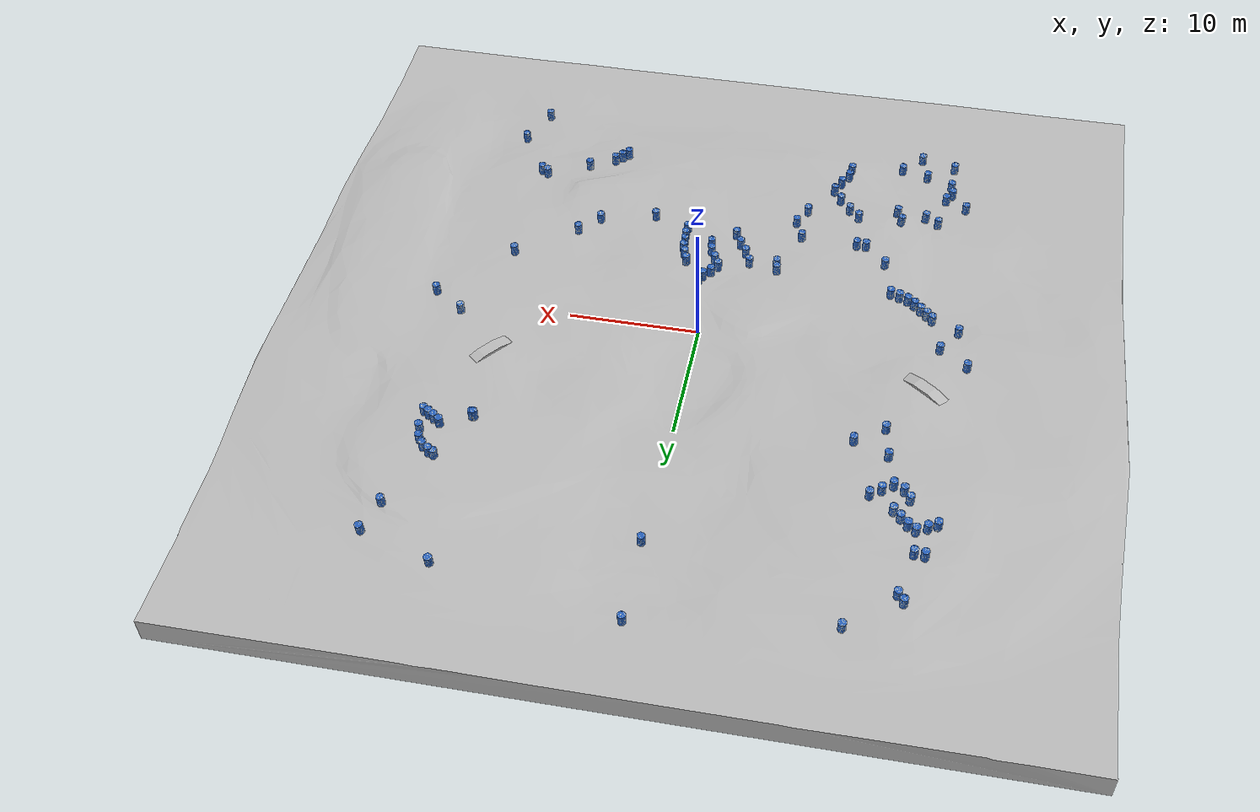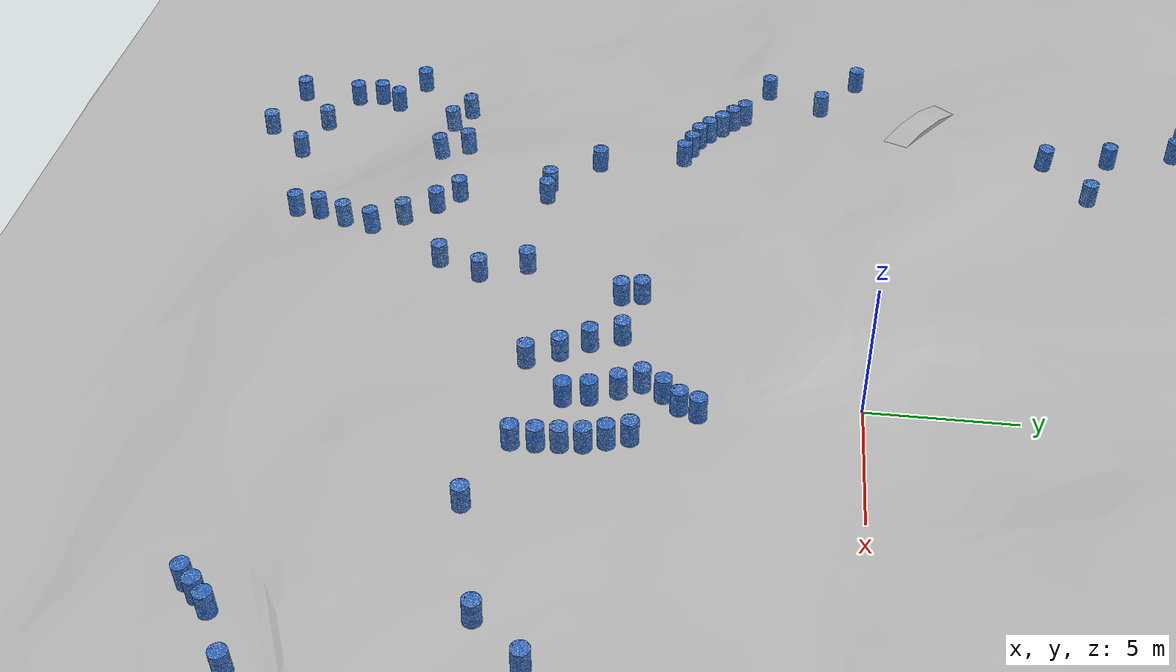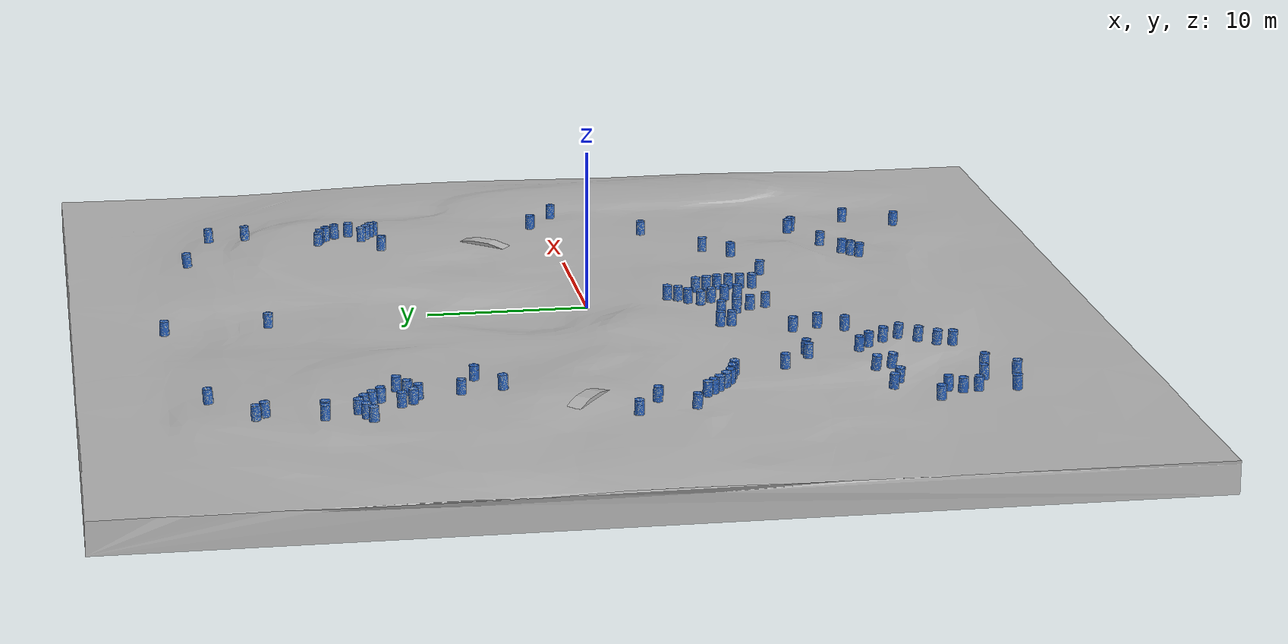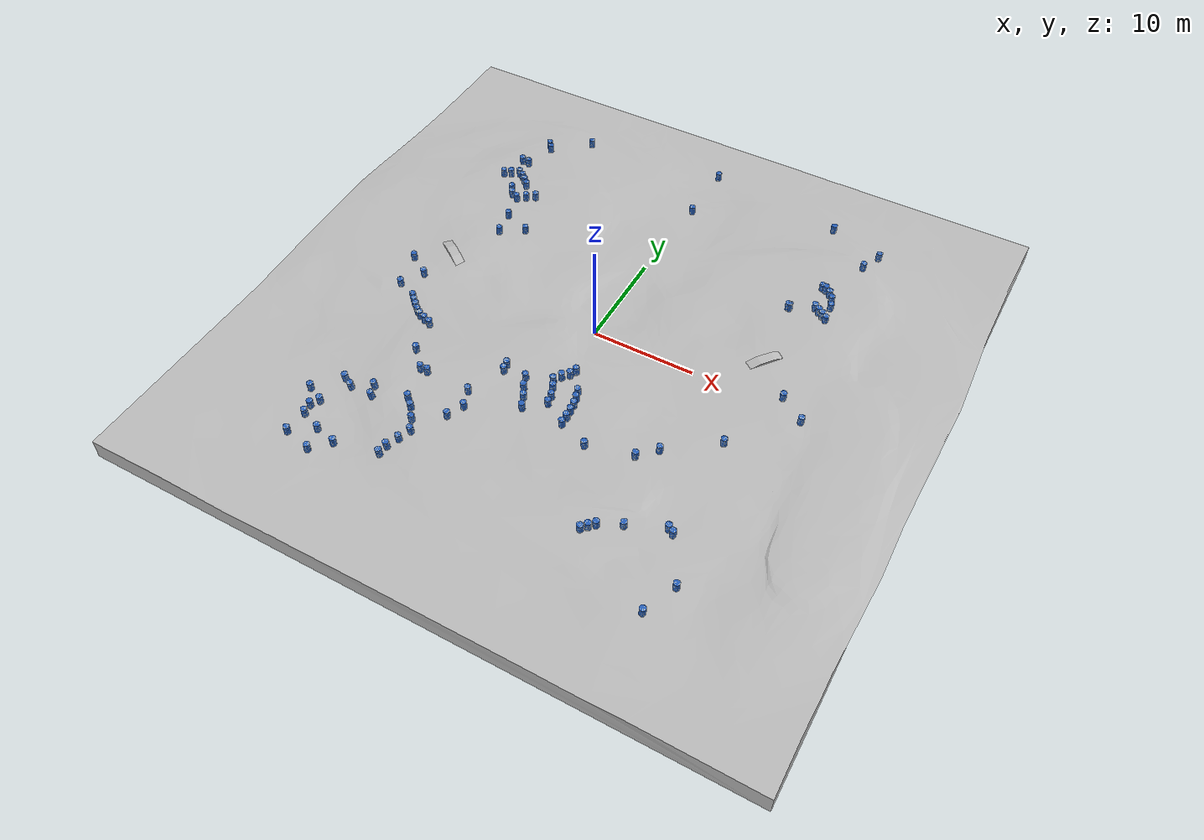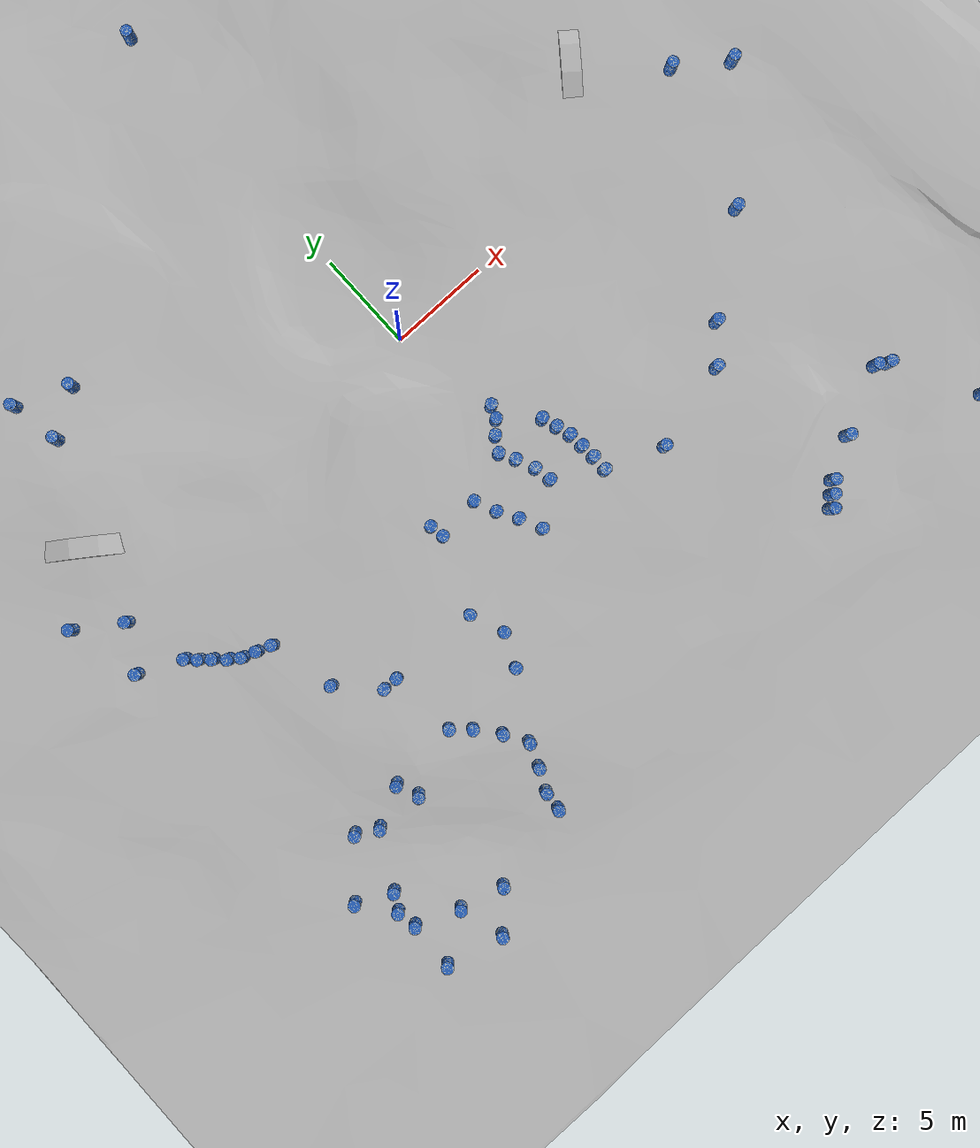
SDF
<sdf version="1.6">
 <world name="default">
  <scene>
   <sky><clouds><speed>12</speed></clouds></sky>
   <ambient>1 1 1 1</ambient>
   <shadows>1</shadows>
   <background>0.7 0.7 0.7 1</background>
  </scene>
  <light name="sun" type="directional">
   <pose>0 0 10 0 -0 0</pose>
   <diffuse>0.8 0.8 0.8 1</diffuse>
   <specular>0.1 0.1 0.1 1</specular>
   <attenuation>
    <range>1000</range>
    <constant>0.9</constant>
    <linear>0.01</linear>
    <quadratic>0.001</quadratic>
   </attenuation>
   <direction>-0.5 0.5 -1</direction>
  </light>
  <model name="autonav_mesh">
   <static>1</static>
   <link name="link">
    <collision name="collision">
     <geometry><mesh><uri>model://autonav_mesh/meshes/autonav_world.dae</uri><scale>1 1 1</scale></mesh></geometry>
     <surface><friction><ode><mu>100</mu><mu2>50</mu2></ode></friction></surface>
    </collision>
    <visual name="visual">
     <cast_shadows>0</cast_shadows>
     <geometry><mesh><uri>model://autonav_mesh/meshes/autonav_world.dae</uri><scale>1 1 1</scale></mesh></geometry>
     <material>
      <script><uri>model://urdf/gazebo.material</uri><name>Gazebo/Texture_autonav</name></script>
     </material>
    </visual>
   </link>
   <pose>0 0 -1.6 0 -0 0</pose>
  </model>
  <model name="ramp_0">
   <static>1</static>
   <link name="link">
    <collision name="collision">
     <geometry><mesh><uri>model://ramp/meshes/ramp.dae</uri><scale>1 1 1</scale></mesh></geometry>
     <surface><friction><ode><mu>100</mu><mu2>50</mu2></ode></friction></surface>
    </collision>
    <visual name="visual">
     <geometry><mesh><uri>model://ramp/meshes/ramp.dae</uri><scale>1 1 1</scale></mesh></geometry>
    </visual>
   </link>
   <pose>16.361 3.674 0 0 0 -0.67</pose>
  </model>
  <model name="ramp_1">
   <static>1</static>
   <link name="link">
    <collision name="collision">
     <geometry><mesh><uri>model://ramp/meshes/ramp.dae</uri><scale>1 1 1</scale></mesh></geometry>
     <surface><friction><ode><mu>100</mu><mu2>50</mu2></ode></friction></surface>
    </collision>
    <visual name="visual">
     <geometry><mesh><uri>model://ramp/meshes/ramp.dae</uri><scale>1 1 1</scale></mesh></geometry>
    </visual>
   </link>
   <pose>-16.608 3.804 0 0 -0 0.955</pose>
  </model>
  <model name="barrel_0">
   <link name="link">
    <inertial>
     <mass>500</mass>
     <inertia><ixx>51.2096</ixx><iyy>51.2096</iyy><izz>25</izz><ixy>0</ixy><ixz>0</ixz><iyz>0</iyz></inertia>
    </inertial>
    <collision name="collision">
     <geometry><mesh><uri>model://barrel/meshes/barrel.dae</uri><scale>1 1 1</scale></mesh></geometry>
    </collision>
    <visual name="visual">
     <geometry><mesh><uri>model://barrel/meshes/barrel.dae</uri><scale>1 1 1</scale></mesh></geometry>
    </visual>
   </link>
   <pose>0.000577 19.6001 -0.368348 -0.013749 0.008261 0.001406</pose>
  </model>
  <model name="barrel_1">
   <link name="link">
    <inertial>
     <mass>500</mass>
     <inertia><ixx>51.2096</ixx><iyy>51.2096</iyy><izz>25</izz><ixy>0</ixy><ixz>0</ixz><iyz>0</iyz></inertia>
    </inertial>
    <collision name="collision">
     <geometry><mesh><uri>model://barrel/meshes/barrel.dae</uri><scale>1 1 1</scale></mesh></geometry>
    </collision>
    <visual name="visual">
     <geometry><mesh><uri>model://barrel/meshes/barrel.dae</uri><scale>1 1 1</scale></mesh></geometry>
    </visual>
   </link>
   <pose>9e-05 26.0002 -0.587822 0.001098 -0.003196 0.000934</pose>
  </model>
  <model name="barrel_2">
   <link name="link">
    <inertial>
     <mass>500</mass>
     <inertia><ixx>51.2096</ixx><iyy>51.2096</iyy><izz>25</izz><ixy>0</ixy><ixz>0</ixz><iyz>0</iyz></inertia>
    </inertial>
    <collision name="collision">
     <geometry><mesh><uri>model://barrel/meshes/barrel.dae</uri><scale>1 1 1</scale></mesh></geometry>
    </collision>
    <visual name="visual">
     <geometry><mesh><uri>model://barrel/meshes/barrel.dae</uri><scale>1 1 1</scale></mesh></geometry>
    </visual>
   </link>
   <pose>13.7842 23.8793 -0.311648 -0.097813 -0.00708 -0.007914</pose>
  </model>
  <model name="barrel_3">
   <link name="link">
    <inertial>
     <mass>500</mass>
     <inertia><ixx>51.2096</ixx><iyy>51.2096</iyy><izz>25</izz><ixy>0</ixy><ixz>0</ixz><iyz>0</iyz></inertia>
    </inertial>
    <collision name="collision">
     <geometry><mesh><uri>model://barrel/meshes/barrel.dae</uri><scale>1 1 1</scale></mesh></geometry>
    </collision>
    <visual name="visual">
     <geometry><mesh><uri>model://barrel/meshes/barrel.dae</uri><scale>1 1 1</scale></mesh></geometry>
    </visual>
   </link>
   <pose>19.182 22.1896 -0.261493 -0.053603 0.029037 0.000883</pose>
  </model>
  <model name="barrel_4">
   <link name="link">
    <inertial>
     <mass>500</mass>
     <inertia><ixx>51.2096</ixx><iyy>51.2096</iyy><izz>25</izz><ixy>0</ixy><ixz>0</ixz><iyz>0</iyz></inertia>
    </inertial>
    <collision name="collision">
     <geometry><mesh><uri>model://barrel/meshes/barrel.dae</uri><scale>1 1 1</scale></mesh></geometry>
    </collision>
    <visual name="visual">
     <geometry><mesh><uri>model://barrel/meshes/barrel.dae</uri><scale>1 1 1</scale></mesh></geometry>
    </visual>
   </link>
   <pose>18.3899 19.8308 0.03271 -0.04712 0.020418 0.006103</pose>
  </model>
  <model name="barrel_5">
   <link name="link">
    <inertial>
     <mass>500</mass>
     <inertia><ixx>51.2096</ixx><iyy>51.2096</iyy><izz>25</izz><ixy>0</ixy><ixz>0</ixz><iyz>0</iyz></inertia>
    </inertial>
    <collision name="collision">
     <geometry><mesh><uri>model://barrel/meshes/barrel.dae</uri><scale>1 1 1</scale></mesh></geometry>
    </collision>
    <visual name="visual">
     <geometry><mesh><uri>model://barrel/meshes/barrel.dae</uri><scale>1 1 1</scale></mesh></geometry>
    </visual>
   </link>
   <pose>15.9586 15.2386 0.040804 -0.005078 -0.00794 -0.245496</pose>
  </model>
  <model name="barrel_6">
   <link name="link">
    <inertial>
     <mass>500</mass>
     <inertia><ixx>51.2096</ixx><iyy>51.2096</iyy><izz>25</izz><ixy>0</ixy><ixz>0</ixz><iyz>0</iyz></inertia>
    </inertial>
    <collision name="collision">
     <geometry><mesh><uri>model://barrel/meshes/barrel.dae</uri><scale>1 1 1</scale></mesh></geometry>
    </collision>
    <visual name="visual">
     <geometry><mesh><uri>model://barrel/meshes/barrel.dae</uri><scale>1 1 1</scale></mesh></geometry>
    </visual>
   </link>
   <pose>16.4874 14.9674 0.14586 -0.006664 0.00198 0.228719</pose>
  </model>
  <model name="barrel_7">
   <link name="link">
    <inertial>
     <mass>500</mass>
     <inertia><ixx>51.2096</ixx><iyy>51.2096</iyy><izz>25</izz><ixy>0</ixy><ixz>0</ixz><iyz>0</iyz></inertia>
    </inertial>
    <collision name="collision">
     <geometry><mesh><uri>model://barrel/meshes/barrel.dae</uri><scale>1 1 1</scale></mesh></geometry>
    </collision>
    <visual name="visual">
     <geometry><mesh><uri>model://barrel/meshes/barrel.dae</uri><scale>1 1 1</scale></mesh></geometry>
    </visual>
   </link>
   <pose>16.9472 14.6117 0.148136 -0.006952 0.000197 -0.031541</pose>
  </model>
  <model name="barrel_8">
   <link name="link">
    <inertial>
     <mass>500</mass>
     <inertia><ixx>51.2096</ixx><iyy>51.2096</iyy><izz>25</izz><ixy>0</ixy><ixz>0</ixz><iyz>0</iyz></inertia>
    </inertial>
    <collision name="collision">
     <geometry><mesh><uri>model://barrel/meshes/barrel.dae</uri><scale>1 1 1</scale></mesh></geometry>
    </collision>
    <visual name="visual">
     <geometry><mesh><uri>model://barrel/meshes/barrel.dae</uri><scale>1 1 1</scale></mesh></geometry>
    </visual>
   </link>
   <pose>17.2991 14.1494 0.150721 -0.005381 0.000334 -0.476369</pose>
  </model>
  <model name="barrel_9">
   <link name="link">
    <inertial>
     <mass>500</mass>
     <inertia><ixx>51.2096</ixx><iyy>51.2096</iyy><izz>25</izz><ixy>0</ixy><ixz>0</ixz><iyz>0</iyz></inertia>
    </inertial>
    <collision name="collision">
     <geometry><mesh><uri>model://barrel/meshes/barrel.dae</uri><scale>1 1 1</scale></mesh></geometry>
    </collision>
    <visual name="visual">
     <geometry><mesh><uri>model://barrel/meshes/barrel.dae</uri><scale>1 1 1</scale></mesh></geometry>
    </visual>
   </link>
   <pose>17.6856 13.0368 0.154801 -0.004634 0.002765 -0.002073</pose>
  </model>
  <model name="barrel_10">
   <link name="link">
    <inertial>
     <mass>500</mass>
     <inertia><ixx>51.2096</ixx><iyy>51.2096</iyy><izz>25</izz><ixy>0</ixy><ixz>0</ixz><iyz>0</iyz></inertia>
    </inertial>
    <collision name="collision">
     <geometry><mesh><uri>model://barrel/meshes/barrel.dae</uri><scale>1 1 1</scale></mesh></geometry>
    </collision>
    <visual name="visual">
     <geometry><mesh><uri>model://barrel/meshes/barrel.dae</uri><scale>1 1 1</scale></mesh></geometry>
    </visual>
   </link>
   <pose>17.9095 11.2902 0.061415 -0.003947 0.003681 0.21033</pose>
  </model>
  <model name="barrel_11">
   <link name="link">
    <inertial>
     <mass>500</mass>
     <inertia><ixx>51.2096</ixx><iyy>51.2096</iyy><izz>25</izz><ixy>0</ixy><ixz>0</ixz><iyz>0</iyz></inertia>
    </inertial>
    <collision name="collision">
     <geometry><mesh><uri>model://barrel/meshes/barrel.dae</uri><scale>1 1 1</scale></mesh></geometry>
    </collision>
    <visual name="visual">
     <geometry><mesh><uri>model://barrel/meshes/barrel.dae</uri><scale>1 1 1</scale></mesh></geometry>
    </visual>
   </link>
   <pose>17.4354 11.5947 0.16217 -0.004174 0.003409 0.146928</pose>
  </model>
  <model name="barrel_12">
   <link name="link">
    <inertial>
     <mass>500</mass>
     <inertia><ixx>51.2096</ixx><iyy>51.2096</iyy><izz>25</izz><ixy>0</ixy><ixz>0</ixz><iyz>0</iyz></inertia>
    </inertial>
    <collision name="collision">
     <geometry><mesh><uri>model://barrel/meshes/barrel.dae</uri><scale>1 1 1</scale></mesh></geometry>
    </collision>
    <visual name="visual">
     <geometry><mesh><uri>model://barrel/meshes/barrel.dae</uri><scale>1 1 1</scale></mesh></geometry>
    </visual>
   </link>
   <pose>16.9418 11.9257 0.162001 -0.004457 0.003008 0.057587</pose>
  </model>
  <model name="barrel_13">
   <link name="link">
    <inertial>
     <mass>500</mass>
     <inertia><ixx>51.2096</ixx><iyy>51.2096</iyy><izz>25</izz><ixy>0</ixy><ixz>0</ixz><iyz>0</iyz></inertia>
    </inertial>
    <collision name="collision">
     <geometry><mesh><uri>model://barrel/meshes/barrel.dae</uri><scale>1 1 1</scale></mesh></geometry>
    </collision>
    <visual name="visual">
     <geometry><mesh><uri>model://barrel/meshes/barrel.dae</uri><scale>1 1 1</scale></mesh></geometry>
    </visual>
   </link>
   <pose>16.4459 12.263 0.160191 -0.002864 -0.001939 0.033093</pose>
  </model>
  <model name="barrel_14">
   <link name="link">
    <inertial>
     <mass>500</mass>
     <inertia><ixx>51.2096</ixx><iyy>51.2096</iyy><izz>25</izz><ixy>0</ixy><ixz>0</ixz><iyz>0</iyz></inertia>
    </inertial>
    <collision name="collision">
     <geometry><mesh><uri>model://barrel/meshes/barrel.dae</uri><scale>1 1 1</scale></mesh></geometry>
    </collision>
    <visual name="visual">
     <geometry><mesh><uri>model://barrel/meshes/barrel.dae</uri><scale>1 1 1</scale></mesh></geometry>
    </visual>
   </link>
   <pose>14.0611 11.3234 0.150776 0.003882 -0.0041 -0.461408</pose>
  </model>
  <model name="barrel_15">
   <link name="link">
    <inertial>
     <mass>500</mass>
     <inertia><ixx>51.2096</ixx><iyy>51.2096</iyy><izz>25</izz><ixy>0</ixy><ixz>0</ixz><iyz>0</iyz></inertia>
    </inertial>
    <collision name="collision">
     <geometry><mesh><uri>model://barrel/meshes/barrel.dae</uri><scale>1 1 1</scale></mesh></geometry>
    </collision>
    <visual name="visual">
     <geometry><mesh><uri>model://barrel/meshes/barrel.dae</uri><scale>1 1 1</scale></mesh></geometry>
    </visual>
   </link>
   <pose>14.6501 11.0516 0.153504 -0.003409 -0.004497 0.945203</pose>
  </model>
  <model name="barrel_16">
   <link name="link">
    <inertial>
     <mass>500</mass>
     <inertia><ixx>51.2096</ixx><iyy>51.2096</iyy><izz>25</izz><ixy>0</ixy><ixz>0</ixz><iyz>0</iyz></inertia>
    </inertial>
    <collision name="collision">
     <geometry><mesh><uri>model://barrel/meshes/barrel.dae</uri><scale>1 1 1</scale></mesh></geometry>
    </collision>
    <visual name="visual">
     <geometry><mesh><uri>model://barrel/meshes/barrel.dae</uri><scale>1 1 1</scale></mesh></geometry>
    </visual>
   </link>
   <pose>-6.64602 -12.0896 -0.065877 0.021904 -0.000621 -0.000895</pose>
  </model>
  <model name="barrel_17">
   <link name="link">
    <inertial>
     <mass>500</mass>
     <inertia><ixx>51.2096</ixx><iyy>51.2096</iyy><izz>25</izz><ixy>0</ixy><ixz>0</ixz><iyz>0</iyz></inertia>
    </inertial>
    <collision name="collision">
     <geometry><mesh><uri>model://barrel/meshes/barrel.dae</uri><scale>1 1 1</scale></mesh></geometry>
    </collision>
    <visual name="visual">
     <geometry><mesh><uri>model://barrel/meshes/barrel.dae</uri><scale>1 1 1</scale></mesh></geometry>
    </visual>
   </link>
   <pose>-6.01499 -13.7526 -0.092026 0.011651 -0.003126 -0.001076</pose>
  </model>
  <model name="barrel_18">
   <link name="link">
    <inertial>
     <mass>500</mass>
     <inertia><ixx>51.2096</ixx><iyy>51.2096</iyy><izz>25</izz><ixy>0</ixy><ixz>0</ixz><iyz>0</iyz></inertia>
    </inertial>
    <collision name="collision">
     <geometry><mesh><uri>model://barrel/meshes/barrel.dae</uri><scale>1 1 1</scale></mesh></geometry>
    </collision>
    <visual name="visual">
     <geometry><mesh><uri>model://barrel/meshes/barrel.dae</uri><scale>1 1 1</scale></mesh></geometry>
    </visual>
   </link>
   <pose>18.1288 0.756798 0.044792 0.003076 -0.000361 0.0009</pose>
  </model>
  <model name="barrel_19">
   <link name="link">
    <inertial>
     <mass>500</mass>
     <inertia><ixx>51.2096</ixx><iyy>51.2096</iyy><izz>25</izz><ixy>0</ixy><ixz>0</ixz><iyz>0</iyz></inertia>
    </inertial>
    <collision name="collision">
     <geometry><mesh><uri>model://barrel/meshes/barrel.dae</uri><scale>1 1 1</scale></mesh></geometry>
    </collision>
    <visual name="visual">
     <geometry><mesh><uri>model://barrel/meshes/barrel.dae</uri><scale>1 1 1</scale></mesh></geometry>
    </visual>
   </link>
   <pose>20.5343 -0.955068 0.017522 0.004462 0.03527 -0.000349</pose>
  </model>
  <model name="barrel_20">
   <link name="link">
    <inertial>
     <mass>500</mass>
     <inertia><ixx>51.2096</ixx><iyy>51.2096</iyy><izz>25</izz><ixy>0</ixy><ixz>0</ixz><iyz>0</iyz></inertia>
    </inertial>
    <collision name="collision">
     <geometry><mesh><uri>model://barrel/meshes/barrel.dae</uri><scale>1 1 1</scale></mesh></geometry>
    </collision>
    <visual name="visual">
     <geometry><mesh><uri>model://barrel/meshes/barrel.dae</uri><scale>1 1 1</scale></mesh></geometry>
    </visual>
   </link>
   <pose>15.6992 -6.35723 0.012643 0.005134 0.002823 4.8e-05</pose>
  </model>
  <model name="barrel_21">
   <link name="link">
    <inertial>
     <mass>500</mass>
     <inertia><ixx>51.2096</ixx><iyy>51.2096</iyy><izz>25</izz><ixy>0</ixy><ixz>0</ixz><iyz>0</iyz></inertia>
    </inertial>
    <collision name="collision">
     <geometry><mesh><uri>model://barrel/meshes/barrel.dae</uri><scale>1 1 1</scale></mesh></geometry>
    </collision>
    <visual name="visual">
     <geometry><mesh><uri>model://barrel/meshes/barrel.dae</uri><scale>1 1 1</scale></mesh></geometry>
    </visual>
   </link>
   <pose>11.2531 -9.72098 0.001207 -0.000622 0.003513 1.9e-05</pose>
  </model>
  <model name="barrel_22">
   <link name="link">
    <inertial>
     <mass>500</mass>
     <inertia><ixx>51.2096</ixx><iyy>51.2096</iyy><izz>25</izz><ixy>0</ixy><ixz>0</ixz><iyz>0</iyz></inertia>
    </inertial>
    <collision name="collision">
     <geometry><mesh><uri>model://barrel/meshes/barrel.dae</uri><scale>1 1 1</scale></mesh></geometry>
    </collision>
    <visual name="visual">
     <geometry><mesh><uri>model://barrel/meshes/barrel.dae</uri><scale>1 1 1</scale></mesh></geometry>
    </visual>
   </link>
   <pose>15.4375 -16.2895 -0.228445 0.025489 0.015645 0.000221</pose>
  </model>
  <model name="barrel_23">
   <link name="link">
    <inertial>
     <mass>500</mass>
     <inertia><ixx>51.2096</ixx><iyy>51.2096</iyy><izz>25</izz><ixy>0</ixy><ixz>0</ixz><iyz>0</iyz></inertia>
    </inertial>
    <collision name="collision">
     <geometry><mesh><uri>model://barrel/meshes/barrel.dae</uri><scale>1 1 1</scale></mesh></geometry>
    </collision>
    <visual name="visual">
     <geometry><mesh><uri>model://barrel/meshes/barrel.dae</uri><scale>1 1 1</scale></mesh></geometry>
    </visual>
   </link>
   <pose>15.9884 -16.6115 -0.243718 0.024704 0.011043 0.004901</pose>
  </model>
  <model name="barrel_24">
   <link name="link">
    <inertial>
     <mass>500</mass>
     <inertia><ixx>51.2096</ixx><iyy>51.2096</iyy><izz>25</izz><ixy>0</ixy><ixz>0</ixz><iyz>0</iyz></inertia>
    </inertial>
    <collision name="collision">
     <geometry><mesh><uri>model://barrel/meshes/barrel.dae</uri><scale>1 1 1</scale></mesh></geometry>
    </collision>
    <visual name="visual">
     <geometry><mesh><uri>model://barrel/meshes/barrel.dae</uri><scale>1 1 1</scale></mesh></geometry>
    </visual>
   </link>
   <pose>18.3608 -20.6973 -0.45242 0.015842 0.026169 -0.001995</pose>
  </model>
  <model name="barrel_25">
   <link name="link">
    <inertial>
     <mass>500</mass>
     <inertia><ixx>51.2096</ixx><iyy>51.2096</iyy><izz>25</izz><ixy>0</ixy><ixz>0</ixz><iyz>0</iyz></inertia>
    </inertial>
    <collision name="collision">
     <geometry><mesh><uri>model://barrel/meshes/barrel.dae</uri><scale>1 1 1</scale></mesh></geometry>
    </collision>
    <visual name="visual">
     <geometry><mesh><uri>model://barrel/meshes/barrel.dae</uri><scale>1 1 1</scale></mesh></geometry>
    </visual>
   </link>
   <pose>17.0741 -23.9449 -0.466777 0.016096 0.014441 -0.00362</pose>
  </model>
  <model name="barrel_26">
   <link name="link">
    <inertial>
     <mass>500</mass>
     <inertia><ixx>51.2096</ixx><iyy>51.2096</iyy><izz>25</izz><ixy>0</ixy><ixz>0</ixz><iyz>0</iyz></inertia>
    </inertial>
    <collision name="collision">
     <geometry><mesh><uri>model://barrel/meshes/barrel.dae</uri><scale>1 1 1</scale></mesh></geometry>
    </collision>
    <visual name="visual">
     <geometry><mesh><uri>model://barrel/meshes/barrel.dae</uri><scale>1 1 1</scale></mesh></geometry>
    </visual>
   </link>
   <pose>12.1238 -17.7903 -0.194908 0.052107 0.034637 -0.033032</pose>
  </model>
  <model name="barrel_27">
   <link name="link">
    <inertial>
     <mass>500</mass>
     <inertia><ixx>51.2096</ixx><iyy>51.2096</iyy><izz>25</izz><ixy>0</ixy><ixz>0</ixz><iyz>0</iyz></inertia>
    </inertial>
    <collision name="collision">
     <geometry><mesh><uri>model://barrel/meshes/barrel.dae</uri><scale>1 1 1</scale></mesh></geometry>
    </collision>
    <visual name="visual">
     <geometry><mesh><uri>model://barrel/meshes/barrel.dae</uri><scale>1 1 1</scale></mesh></geometry>
    </visual>
   </link>
   <pose>10.1544 -18.8418 -0.192373 0.050254 0.017038 -0.013136</pose>
  </model>
  <model name="barrel_28">
   <link name="link">
    <inertial>
     <mass>500</mass>
     <inertia><ixx>51.2096</ixx><iyy>51.2096</iyy><izz>25</izz><ixy>0</ixy><ixz>0</ixz><iyz>0</iyz></inertia>
    </inertial>
    <collision name="collision">
     <geometry><mesh><uri>model://barrel/meshes/barrel.dae</uri><scale>1 1 1</scale></mesh></geometry>
    </collision>
    <visual name="visual">
     <geometry><mesh><uri>model://barrel/meshes/barrel.dae</uri><scale>1 1 1</scale></mesh></geometry>
    </visual>
   </link>
   <pose>9.65125 -19.314 -0.207993 0.050227 0.017133 -0.015108</pose>
  </model>
  <model name="barrel_29">
   <link name="link">
    <inertial>
     <mass>500</mass>
     <inertia><ixx>51.2096</ixx><iyy>51.2096</iyy><izz>25</izz><ixy>0</ixy><ixz>0</ixz><iyz>0</iyz></inertia>
    </inertial>
    <collision name="collision">
     <geometry><mesh><uri>model://barrel/meshes/barrel.dae</uri><scale>1 1 1</scale></mesh></geometry>
    </collision>
    <visual name="visual">
     <geometry><mesh><uri>model://barrel/meshes/barrel.dae</uri><scale>1 1 1</scale></mesh></geometry>
    </visual>
   </link>
   <pose>9.18372 -19.7763 -0.227088 0.070803 0.016683 -0.010783</pose>
  </model>
  <model name="barrel_30">
   <link name="link">
    <inertial>
     <mass>500</mass>
     <inertia><ixx>51.2096</ixx><iyy>51.2096</iyy><izz>25</izz><ixy>0</ixy><ixz>0</ixz><iyz>0</iyz></inertia>
    </inertial>
    <collision name="collision">
     <geometry><mesh><uri>model://barrel/meshes/barrel.dae</uri><scale>1 1 1</scale></mesh></geometry>
    </collision>
    <visual name="visual">
     <geometry><mesh><uri>model://barrel/meshes/barrel.dae</uri><scale>1 1 1</scale></mesh></geometry>
    </visual>
   </link>
   <pose>9.74218 -11.3225 0.02096 -0.012189 0.00495 -1.7e-05</pose>
  </model>
  <model name="barrel_31">
   <link name="link">
    <inertial>
     <mass>500</mass>
     <inertia><ixx>51.2096</ixx><iyy>51.2096</iyy><izz>25</izz><ixy>0</ixy><ixz>0</ixz><iyz>0</iyz></inertia>
    </inertial>
    <collision name="collision">
     <geometry><mesh><uri>model://barrel/meshes/barrel.dae</uri><scale>1 1 1</scale></mesh></geometry>
    </collision>
    <visual name="visual">
     <geometry><mesh><uri>model://barrel/meshes/barrel.dae</uri><scale>1 1 1</scale></mesh></geometry>
    </visual>
   </link>
   <pose>5.39296 -12.4014 0.018129 0.010171 -0.002475 7.6e-05</pose>
  </model>
  <model name="barrel_32">
   <link name="link">
    <inertial>
     <mass>500</mass>
     <inertia><ixx>51.2096</ixx><iyy>51.2096</iyy><izz>25</izz><ixy>0</ixy><ixz>0</ixz><iyz>0</iyz></inertia>
    </inertial>
    <collision name="collision">
     <geometry><mesh><uri>model://barrel/meshes/barrel.dae</uri><scale>1 1 1</scale></mesh></geometry>
    </collision>
    <visual name="visual">
     <geometry><mesh><uri>model://barrel/meshes/barrel.dae</uri><scale>1 1 1</scale></mesh></geometry>
    </visual>
   </link>
   <pose>2.55652 -11.3385 0.015993 0.012526 -0.012887 2.5e-05</pose>
  </model>
  <model name="barrel_33">
   <link name="link">
    <inertial>
     <mass>500</mass>
     <inertia><ixx>51.2096</ixx><iyy>51.2096</iyy><izz>25</izz><ixy>0</ixy><ixz>0</ixz><iyz>0</iyz></inertia>
    </inertial>
    <collision name="collision">
     <geometry><mesh><uri>model://barrel/meshes/barrel.dae</uri><scale>1 1 1</scale></mesh></geometry>
    </collision>
    <visual name="visual">
     <geometry><mesh><uri>model://barrel/meshes/barrel.dae</uri><scale>1 1 1</scale></mesh></geometry>
    </visual>
   </link>
   <pose>2.56652 -10.5277 0.02611 0.012632 -0.011815 -2e-06</pose>
  </model>
  <model name="barrel_34">
   <link name="link">
    <inertial>
     <mass>500</mass>
     <inertia><ixx>51.2096</ixx><iyy>51.2096</iyy><izz>25</izz><ixy>0</ixy><ixz>0</ixz><iyz>0</iyz></inertia>
    </inertial>
    <collision name="collision">
     <geometry><mesh><uri>model://barrel/meshes/barrel.dae</uri><scale>1 1 1</scale></mesh></geometry>
    </collision>
    <visual name="visual">
     <geometry><mesh><uri>model://barrel/meshes/barrel.dae</uri><scale>1 1 1</scale></mesh></geometry>
    </visual>
   </link>
   <pose>2.52148 -9.78355 0.036837 0.01914 -0.013142 -0.000263</pose>
  </model>
  <model name="barrel_35">
   <link name="link">
    <inertial>
     <mass>500</mass>
     <inertia><ixx>51.2096</ixx><iyy>51.2096</iyy><izz>25</izz><ixy>0</ixy><ixz>0</ixz><iyz>0</iyz></inertia>
    </inertial>
    <collision name="collision">
     <geometry><mesh><uri>model://barrel/meshes/barrel.dae</uri><scale>1 1 1</scale></mesh></geometry>
    </collision>
    <visual name="visual">
     <geometry><mesh><uri>model://barrel/meshes/barrel.dae</uri><scale>1 1 1</scale></mesh></geometry>
    </visual>
   </link>
   <pose>2.41641 -8.98886 0.052496 0.02482 -0.009879 -0.161014</pose>
  </model>
  <model name="barrel_36">
   <link name="link">
    <inertial>
     <mass>500</mass>
     <inertia><ixx>51.2096</ixx><iyy>51.2096</iyy><izz>25</izz><ixy>0</ixy><ixz>0</ixz><iyz>0</iyz></inertia>
    </inertial>
    <collision name="collision">
     <geometry><mesh><uri>model://barrel/meshes/barrel.dae</uri><scale>1 1 1</scale></mesh></geometry>
    </collision>
    <visual name="visual">
     <geometry><mesh><uri>model://barrel/meshes/barrel.dae</uri><scale>1 1 1</scale></mesh></geometry>
    </visual>
   </link>
   <pose>2.18789 -8.24474 0.066415 0.025572 -0.007711 -0.246792</pose>
  </model>
  <model name="barrel_37">
   <link name="link">
    <inertial>
     <mass>500</mass>
     <inertia><ixx>51.2096</ixx><iyy>51.2096</iyy><izz>25</izz><ixy>0</ixy><ixz>0</ixz><iyz>0</iyz></inertia>
    </inertial>
    <collision name="collision">
     <geometry><mesh><uri>model://barrel/meshes/barrel.dae</uri><scale>1 1 1</scale></mesh></geometry>
    </collision>
    <visual name="visual">
     <geometry><mesh><uri>model://barrel/meshes/barrel.dae</uri><scale>1 1 1</scale></mesh></geometry>
    </visual>
   </link>
   <pose>2.00718 -7.6034 0.074873 0.005774 -0.016323 -0.021645</pose>
  </model>
  <model name="barrel_38">
   <link name="link">
    <inertial>
     <mass>500</mass>
     <inertia><ixx>51.2096</ixx><iyy>51.2096</iyy><izz>25</izz><ixy>0</ixy><ixz>0</ixz><iyz>0</iyz></inertia>
    </inertial>
    <collision name="collision">
     <geometry><mesh><uri>model://barrel/meshes/barrel.dae</uri><scale>1 1 1</scale></mesh></geometry>
    </collision>
    <visual name="visual">
     <geometry><mesh><uri>model://barrel/meshes/barrel.dae</uri><scale>1 1 1</scale></mesh></geometry>
    </visual>
   </link>
   <pose>0.345676 -9.95051 0.00928 0.015744 -0.011044 -7e-06</pose>
  </model>
  <model name="barrel_39">
   <link name="link">
    <inertial>
     <mass>500</mass>
     <inertia><ixx>51.2096</ixx><iyy>51.2096</iyy><izz>25</izz><ixy>0</ixy><ixz>0</ixz><iyz>0</iyz></inertia>
    </inertial>
    <collision name="collision">
     <geometry><mesh><uri>model://barrel/meshes/barrel.dae</uri><scale>1 1 1</scale></mesh></geometry>
    </collision>
    <visual name="visual">
     <geometry><mesh><uri>model://barrel/meshes/barrel.dae</uri><scale>1 1 1</scale></mesh></geometry>
    </visual>
   </link>
   <pose>0.194539 -9.10177 0.021509 0.016684 -0.010967 6.1e-05</pose>
  </model>
  <model name="barrel_40">
   <link name="link">
    <inertial>
     <mass>500</mass>
     <inertia><ixx>51.2096</ixx><iyy>51.2096</iyy><izz>25</izz><ixy>0</ixy><ixz>0</ixz><iyz>0</iyz></inertia>
    </inertial>
    <collision name="collision">
     <geometry><mesh><uri>model://barrel/meshes/barrel.dae</uri><scale>1 1 1</scale></mesh></geometry>
    </collision>
    <visual name="visual">
     <geometry><mesh><uri>model://barrel/meshes/barrel.dae</uri><scale>1 1 1</scale></mesh></geometry>
    </visual>
   </link>
   <pose>-0.196327 -8.1814 0.035138 0.022914 -0.013727 -0.000318</pose>
  </model>
  <model name="barrel_41">
   <link name="link">
    <inertial>
     <mass>500</mass>
     <inertia><ixx>51.2096</ixx><iyy>51.2096</iyy><izz>25</izz><ixy>0</ixy><ixz>0</ixz><iyz>0</iyz></inertia>
    </inertial>
    <collision name="collision">
     <geometry><mesh><uri>model://barrel/meshes/barrel.dae</uri><scale>1 1 1</scale></mesh></geometry>
    </collision>
    <visual name="visual">
     <geometry><mesh><uri>model://barrel/meshes/barrel.dae</uri><scale>1 1 1</scale></mesh></geometry>
    </visual>
   </link>
   <pose>-0.593189 -7.45294 0.033692 0.006171 -0.013896 0.000365</pose>
  </model>
  <model name="barrel_42">
   <link name="link">
    <inertial>
     <mass>500</mass>
     <inertia><ixx>51.2096</ixx><iyy>51.2096</iyy><izz>25</izz><ixy>0</ixy><ixz>0</ixz><iyz>0</iyz></inertia>
    </inertial>
    <collision name="collision">
     <geometry><mesh><uri>model://barrel/meshes/barrel.dae</uri><scale>1 1 1</scale></mesh></geometry>
    </collision>
    <visual name="visual">
     <geometry><mesh><uri>model://barrel/meshes/barrel.dae</uri><scale>1 1 1</scale></mesh></geometry>
    </visual>
   </link>
   <pose>-0.145362 -6.7328 0.044187 0.005382 -0.016456 0.002248</pose>
  </model>
  <model name="barrel_43">
   <link name="link">
    <inertial>
     <mass>500</mass>
     <inertia><ixx>51.2096</ixx><iyy>51.2096</iyy><izz>25</izz><ixy>0</ixy><ixz>0</ixz><iyz>0</iyz></inertia>
    </inertial>
    <collision name="collision">
     <geometry><mesh><uri>model://barrel/meshes/barrel.dae</uri><scale>1 1 1</scale></mesh></geometry>
    </collision>
    <visual name="visual">
     <geometry><mesh><uri>model://barrel/meshes/barrel.dae</uri><scale>1 1 1</scale></mesh></geometry>
    </visual>
   </link>
   <pose>0.35669 -6.12448 0.056118 0.010374 -0.013184 -0.16539</pose>
  </model>
  <model name="barrel_44">
   <link name="link">
    <inertial>
     <mass>500</mass>
     <inertia><ixx>51.2096</ixx><iyy>51.2096</iyy><izz>25</izz><ixy>0</ixy><ixz>0</ixz><iyz>0</iyz></inertia>
    </inertial>
    <collision name="collision">
     <geometry><mesh><uri>model://barrel/meshes/barrel.dae</uri><scale>1 1 1</scale></mesh></geometry>
    </collision>
    <visual name="visual">
     <geometry><mesh><uri>model://barrel/meshes/barrel.dae</uri><scale>1 1 1</scale></mesh></geometry>
    </visual>
   </link>
   <pose>0.705253 -5.57591 0.066175 0.012325 -0.013779 0.109545</pose>
  </model>
  <model name="barrel_45">
   <link name="link">
    <inertial>
     <mass>500</mass>
     <inertia><ixx>51.2096</ixx><iyy>51.2096</iyy><izz>25</izz><ixy>0</ixy><ixz>0</ixz><iyz>0</iyz></inertia>
    </inertial>
    <collision name="collision">
     <geometry><mesh><uri>model://barrel/meshes/barrel.dae</uri><scale>1 1 1</scale></mesh></geometry>
    </collision>
    <visual name="visual">
     <geometry><mesh><uri>model://barrel/meshes/barrel.dae</uri><scale>1 1 1</scale></mesh></geometry>
    </visual>
   </link>
   <pose>-1.45042 -11.4062 -0.033602 0.015768 -0.011614 0.001184</pose>
  </model>
  <model name="barrel_46">
   <link name="link">
    <inertial>
     <mass>500</mass>
     <inertia><ixx>51.2096</ixx><iyy>51.2096</iyy><izz>25</izz><ixy>0</ixy><ixz>0</ixz><iyz>0</iyz></inertia>
    </inertial>
    <collision name="collision">
     <geometry><mesh><uri>model://barrel/meshes/barrel.dae</uri><scale>1 1 1</scale></mesh></geometry>
    </collision>
    <visual name="visual">
     <geometry><mesh><uri>model://barrel/meshes/barrel.dae</uri><scale>1 1 1</scale></mesh></geometry>
    </visual>
   </link>
   <pose>-1.94725 -10.3264 -0.019928 0.019597 -0.007616 0.000982</pose>
  </model>
  <model name="barrel_47">
   <link name="link">
    <inertial>
     <mass>500</mass>
     <inertia><ixx>51.2096</ixx><iyy>51.2096</iyy><izz>25</izz><ixy>0</ixy><ixz>0</ixz><iyz>0</iyz></inertia>
    </inertial>
    <collision name="collision">
     <geometry><mesh><uri>model://barrel/meshes/barrel.dae</uri><scale>1 1 1</scale></mesh></geometry>
    </collision>
    <visual name="visual">
     <geometry><mesh><uri>model://barrel/meshes/barrel.dae</uri><scale>1 1 1</scale></mesh></geometry>
    </visual>
   </link>
   <pose>-2.50828 -9.3786 -0.00491 0.020369 -0.007217 0.000659</pose>
  </model>
  <model name="barrel_48">
   <link name="link">
    <inertial>
     <mass>500</mass>
     <inertia><ixx>51.2096</ixx><iyy>51.2096</iyy><izz>25</izz><ixy>0</ixy><ixz>0</ixz><iyz>0</iyz></inertia>
    </inertial>
    <collision name="collision">
     <geometry><mesh><uri>model://barrel/meshes/barrel.dae</uri><scale>1 1 1</scale></mesh></geometry>
    </collision>
    <visual name="visual">
     <geometry><mesh><uri>model://barrel/meshes/barrel.dae</uri><scale>1 1 1</scale></mesh></geometry>
    </visual>
   </link>
   <pose>-2.95911 -8.31217 0.018698 0.030407 0.002928 -0.001487</pose>
  </model>
  <model name="barrel_49">
   <link name="link">
    <inertial>
     <mass>500</mass>
     <inertia><ixx>51.2096</ixx><iyy>51.2096</iyy><izz>25</izz><ixy>0</ixy><ixz>0</ixz><iyz>0</iyz></inertia>
    </inertial>
    <collision name="collision">
     <geometry><mesh><uri>model://barrel/meshes/barrel.dae</uri><scale>1 1 1</scale></mesh></geometry>
    </collision>
    <visual name="visual">
     <geometry><mesh><uri>model://barrel/meshes/barrel.dae</uri><scale>1 1 1</scale></mesh></geometry>
    </visual>
   </link>
   <pose>-5.12662 -8.55463 0.022376 0.032821 0.006745 0.00065</pose>
  </model>
  <model name="barrel_50">
   <link name="link">
    <inertial>
     <mass>500</mass>
     <inertia><ixx>51.2096</ixx><iyy>51.2096</iyy><izz>25</izz><ixy>0</ixy><ixz>0</ixz><iyz>0</iyz></inertia>
    </inertial>
    <collision name="collision">
     <geometry><mesh><uri>model://barrel/meshes/barrel.dae</uri><scale>1 1 1</scale></mesh></geometry>
    </collision>
    <visual name="visual">
     <geometry><mesh><uri>model://barrel/meshes/barrel.dae</uri><scale>1 1 1</scale></mesh></geometry>
    </visual>
   </link>
   <pose>-5.21125 -7.86601 0.047058 0.038472 0.003077 0.096041</pose>
  </model>
  <model name="barrel_51">
   <link name="link">
    <inertial>
     <mass>500</mass>
     <inertia><ixx>51.2096</ixx><iyy>51.2096</iyy><izz>25</izz><ixy>0</ixy><ixz>0</ixz><iyz>0</iyz></inertia>
    </inertial>
    <collision name="collision">
     <geometry><mesh><uri>model://barrel/meshes/barrel.dae</uri><scale>1 1 1</scale></mesh></geometry>
    </collision>
    <visual name="visual">
     <geometry><mesh><uri>model://barrel/meshes/barrel.dae</uri><scale>1 1 1</scale></mesh></geometry>
    </visual>
   </link>
   <pose>-6.72808 -15.3163 -0.115707 0.014954 -0.00473 -0.000122</pose>
  </model>
  <model name="barrel_52">
   <link name="link">
    <inertial>
     <mass>500</mass>
     <inertia><ixx>51.2096</ixx><iyy>51.2096</iyy><izz>25</izz><ixy>0</ixy><ixz>0</ixz><iyz>0</iyz></inertia>
    </inertial>
    <collision name="collision">
     <geometry><mesh><uri>model://barrel/meshes/barrel.dae</uri><scale>1 1 1</scale></mesh></geometry>
    </collision>
    <visual name="visual">
     <geometry><mesh><uri>model://barrel/meshes/barrel.dae</uri><scale>1 1 1</scale></mesh></geometry>
    </visual>
   </link>
   <pose>-10.8975 -15.3032 -0.124026 0.033459 0.001308 -0.004688</pose>
  </model>
  <model name="barrel_53">
   <link name="link">
    <inertial>
     <mass>500</mass>
     <inertia><ixx>51.2096</ixx><iyy>51.2096</iyy><izz>25</izz><ixy>0</ixy><ixz>0</ixz><iyz>0</iyz></inertia>
    </inertial>
    <collision name="collision">
     <geometry><mesh><uri>model://barrel/meshes/barrel.dae</uri><scale>1 1 1</scale></mesh></geometry>
    </collision>
    <visual name="visual">
     <geometry><mesh><uri>model://barrel/meshes/barrel.dae</uri><scale>1 1 1</scale></mesh></geometry>
    </visual>
   </link>
   <pose>-10.0733 -16.0535 -0.139344 0.027143 -0.010919 -0.000439</pose>
  </model>
  <model name="barrel_54">
   <link name="link">
    <inertial>
     <mass>500</mass>
     <inertia><ixx>51.2096</ixx><iyy>51.2096</iyy><izz>25</izz><ixy>0</ixy><ixz>0</ixz><iyz>0</iyz></inertia>
    </inertial>
    <collision name="collision">
     <geometry><mesh><uri>model://barrel/meshes/barrel.dae</uri><scale>1 1 1</scale></mesh></geometry>
    </collision>
    <visual name="visual">
     <geometry><mesh><uri>model://barrel/meshes/barrel.dae</uri><scale>1 1 1</scale></mesh></geometry>
    </visual>
   </link>
   <pose>-9.21448 -17.1241 -0.161573 0.048807 -0.01323 -0.032807</pose>
  </model>
  <model name="barrel_55">
   <link name="link">
    <inertial>
     <mass>500</mass>
     <inertia><ixx>51.2096</ixx><iyy>51.2096</iyy><izz>25</izz><ixy>0</ixy><ixz>0</ixz><iyz>0</iyz></inertia>
    </inertial>
    <collision name="collision">
     <geometry><mesh><uri>model://barrel/meshes/barrel.dae</uri><scale>1 1 1</scale></mesh></geometry>
    </collision>
    <visual name="visual">
     <geometry><mesh><uri>model://barrel/meshes/barrel.dae</uri><scale>1 1 1</scale></mesh></geometry>
    </visual>
   </link>
   <pose>-8.55343 -18.2093 -0.206495 0.082826 -0.037746 -0.033733</pose>
  </model>
  <model name="barrel_56">
   <link name="link">
    <inertial>
     <mass>500</mass>
     <inertia><ixx>51.2096</ixx><iyy>51.2096</iyy><izz>25</izz><ixy>0</ixy><ixz>0</ixz><iyz>0</iyz></inertia>
    </inertial>
    <collision name="collision">
     <geometry><mesh><uri>model://barrel/meshes/barrel.dae</uri><scale>1 1 1</scale></mesh></geometry>
    </collision>
    <visual name="visual">
     <geometry><mesh><uri>model://barrel/meshes/barrel.dae</uri><scale>1 1 1</scale></mesh></geometry>
    </visual>
   </link>
   <pose>-9.00839 -19.3575 -0.309523 0.072064 -0.03823 -0.050175</pose>
  </model>
  <model name="barrel_57">
   <link name="link">
    <inertial>
     <mass>500</mass>
     <inertia><ixx>51.2096</ixx><iyy>51.2096</iyy><izz>25</izz><ixy>0</ixy><ixz>0</ixz><iyz>0</iyz></inertia>
    </inertial>
    <collision name="collision">
     <geometry><mesh><uri>model://barrel/meshes/barrel.dae</uri><scale>1 1 1</scale></mesh></geometry>
    </collision>
    <visual name="visual">
     <geometry><mesh><uri>model://barrel/meshes/barrel.dae</uri><scale>1 1 1</scale></mesh></geometry>
    </visual>
   </link>
   <pose>-9.55684 -20.3951 -0.401337 0.057824 -0.034974 -0.187496</pose>
  </model>
  <model name="barrel_58">
   <link name="link">
    <inertial>
     <mass>500</mass>
     <inertia><ixx>51.2096</ixx><iyy>51.2096</iyy><izz>25</izz><ixy>0</ixy><ixz>0</ixz><iyz>0</iyz></inertia>
    </inertial>
    <collision name="collision">
     <geometry><mesh><uri>model://barrel/meshes/barrel.dae</uri><scale>1 1 1</scale></mesh></geometry>
    </collision>
    <visual name="visual">
     <geometry><mesh><uri>model://barrel/meshes/barrel.dae</uri><scale>1 1 1</scale></mesh></geometry>
    </visual>
   </link>
   <pose>-9.59353 -21.4303 -0.442766 0.030145 -0.046267 0.080838</pose>
  </model>
  <model name="barrel_59">
   <link name="link">
    <inertial>
     <mass>500</mass>
     <inertia><ixx>51.2096</ixx><iyy>51.2096</iyy><izz>25</izz><ixy>0</ixy><ixz>0</ixz><iyz>0</iyz></inertia>
    </inertial>
    <collision name="collision">
     <geometry><mesh><uri>model://barrel/meshes/barrel.dae</uri><scale>1 1 1</scale></mesh></geometry>
    </collision>
    <visual name="visual">
     <geometry><mesh><uri>model://barrel/meshes/barrel.dae</uri><scale>1 1 1</scale></mesh></geometry>
    </visual>
   </link>
   <pose>-13.875 -22.3191 -0.575805 0.002163 -0.002343 -0.000245</pose>
  </model>
  <model name="barrel_60">
   <link name="link">
    <inertial>
     <mass>500</mass>
     <inertia><ixx>51.2096</ixx><iyy>51.2096</iyy><izz>25</izz><ixy>0</ixy><ixz>0</ixz><iyz>0</iyz></inertia>
    </inertial>
    <collision name="collision">
     <geometry><mesh><uri>model://barrel/meshes/barrel.dae</uri><scale>1 1 1</scale></mesh></geometry>
    </collision>
    <visual name="visual">
     <geometry><mesh><uri>model://barrel/meshes/barrel.dae</uri><scale>1 1 1</scale></mesh></geometry>
    </visual>
   </link>
   <pose>-16.001 -21.75 -0.576353 -0.000706 -0.00103 0</pose>
  </model>
  <model name="barrel_61">
   <link name="link">
    <inertial>
     <mass>500</mass>
     <inertia><ixx>51.2096</ixx><iyy>51.2096</iyy><izz>25</izz><ixy>0</ixy><ixz>0</ixz><iyz>0</iyz></inertia>
    </inertial>
    <collision name="collision">
     <geometry><mesh><uri>model://barrel/meshes/barrel.dae</uri><scale>1 1 1</scale></mesh></geometry>
    </collision>
    <visual name="visual">
     <geometry><mesh><uri>model://barrel/meshes/barrel.dae</uri><scale>1 1 1</scale></mesh></geometry>
    </visual>
   </link>
   <pose>-15.407 -23.9259 -0.570871 -0.003247 0.001065 0.000139</pose>
  </model>
  <model name="barrel_62">
   <link name="link">
    <inertial>
     <mass>500</mass>
     <inertia><ixx>51.2096</ixx><iyy>51.2096</iyy><izz>25</izz><ixy>0</ixy><ixz>0</ixz><iyz>0</iyz></inertia>
    </inertial>
    <collision name="collision">
     <geometry><mesh><uri>model://barrel/meshes/barrel.dae</uri><scale>1 1 1</scale></mesh></geometry>
    </collision>
    <visual name="visual">
     <geometry><mesh><uri>model://barrel/meshes/barrel.dae</uri><scale>1 1 1</scale></mesh></geometry>
    </visual>
   </link>
   <pose>-18.1601 -23.218 -0.576827 3.7e-05 -0.00466 -3.8e-05</pose>
  </model>
  <model name="barrel_63">
   <link name="link">
    <inertial>
     <mass>500</mass>
     <inertia><ixx>51.2096</ixx><iyy>51.2096</iyy><izz>25</izz><ixy>0</ixy><ixz>0</ixz><iyz>0</iyz></inertia>
    </inertial>
    <collision name="collision">
     <geometry><mesh><uri>model://barrel/meshes/barrel.dae</uri><scale>1 1 1</scale></mesh></geometry>
    </collision>
    <visual name="visual">
     <geometry><mesh><uri>model://barrel/meshes/barrel.dae</uri><scale>1 1 1</scale></mesh></geometry>
    </visual>
   </link>
   <pose>-18.0689 -20.9104 -0.57506 0.003415 -0.001781 -0.000817</pose>
  </model>
  <model name="barrel_64">
   <link name="link">
    <inertial>
     <mass>500</mass>
     <inertia><ixx>51.2096</ixx><iyy>51.2096</iyy><izz>25</izz><ixy>0</ixy><ixz>0</ixz><iyz>0</iyz></inertia>
    </inertial>
    <collision name="collision">
     <geometry><mesh><uri>model://barrel/meshes/barrel.dae</uri><scale>1 1 1</scale></mesh></geometry>
    </collision>
    <visual name="visual">
     <geometry><mesh><uri>model://barrel/meshes/barrel.dae</uri><scale>1 1 1</scale></mesh></geometry>
    </visual>
   </link>
   <pose>-18.2219 -19.9213 -0.568826 0.007637 0.000363 -0.001259</pose>
  </model>
  <model name="barrel_65">
   <link name="link">
    <inertial>
     <mass>500</mass>
     <inertia><ixx>51.2096</ixx><iyy>51.2096</iyy><izz>25</izz><ixy>0</ixy><ixz>0</ixz><iyz>0</iyz></inertia>
    </inertial>
    <collision name="collision">
     <geometry><mesh><uri>model://barrel/meshes/barrel.dae</uri><scale>1 1 1</scale></mesh></geometry>
    </collision>
    <visual name="visual">
     <geometry><mesh><uri>model://barrel/meshes/barrel.dae</uri><scale>1 1 1</scale></mesh></geometry>
    </visual>
   </link>
   <pose>-17.763 -19.1232 -0.562893 0.007637 0.000353 -0.000114</pose>
  </model>
  <model name="barrel_66">
   <link name="link">
    <inertial>
     <mass>500</mass>
     <inertia><ixx>51.2096</ixx><iyy>51.2096</iyy><izz>25</izz><ixy>0</ixy><ixz>0</ixz><iyz>0</iyz></inertia>
    </inertial>
    <collision name="collision">
     <geometry><mesh><uri>model://barrel/meshes/barrel.dae</uri><scale>1 1 1</scale></mesh></geometry>
    </collision>
    <visual name="visual">
     <geometry><mesh><uri>model://barrel/meshes/barrel.dae</uri><scale>1 1 1</scale></mesh></geometry>
    </visual>
   </link>
   <pose>-19.4458 -18.3063 -0.550538 0.015452 0.001383 -0.000459</pose>
  </model>
  <model name="barrel_67">
   <link name="link">
    <inertial>
     <mass>500</mass>
     <inertia><ixx>51.2096</ixx><iyy>51.2096</iyy><izz>25</izz><ixy>0</ixy><ixz>0</ixz><iyz>0</iyz></inertia>
    </inertial>
    <collision name="collision">
     <geometry><mesh><uri>model://barrel/meshes/barrel.dae</uri><scale>1 1 1</scale></mesh></geometry>
    </collision>
    <visual name="visual">
     <geometry><mesh><uri>model://barrel/meshes/barrel.dae</uri><scale>1 1 1</scale></mesh></geometry>
    </visual>
   </link>
   <pose>-17.3115 -15.9549 -0.454608 0.06362 -0.032013 0.009863</pose>
  </model>
  <model name="barrel_68">
   <link name="link">
    <inertial>
     <mass>500</mass>
     <inertia><ixx>51.2096</ixx><iyy>51.2096</iyy><izz>25</izz><ixy>0</ixy><ixz>0</ixz><iyz>0</iyz></inertia>
    </inertial>
    <collision name="collision">
     <geometry><mesh><uri>model://barrel/meshes/barrel.dae</uri><scale>1 1 1</scale></mesh></geometry>
    </collision>
    <visual name="visual">
     <geometry><mesh><uri>model://barrel/meshes/barrel.dae</uri><scale>1 1 1</scale></mesh></geometry>
    </visual>
   </link>
   <pose>-16.2633 -16.5023 -0.452354 0.080051 -0.048839 -0.016406</pose>
  </model>
  <model name="barrel_69">
   <link name="link">
    <inertial>
     <mass>500</mass>
     <inertia><ixx>51.2096</ixx><iyy>51.2096</iyy><izz>25</izz><ixy>0</ixy><ixz>0</ixz><iyz>0</iyz></inertia>
    </inertial>
    <collision name="collision">
     <geometry><mesh><uri>model://barrel/meshes/barrel.dae</uri><scale>1 1 1</scale></mesh></geometry>
    </collision>
    <visual name="visual">
     <geometry><mesh><uri>model://barrel/meshes/barrel.dae</uri><scale>1 1 1</scale></mesh></geometry>
    </visual>
   </link>
   <pose>-13.9335 -16.579 -0.315382 0.113859 -0.062859 0.001258</pose>
  </model>
  <model name="barrel_70">
   <link name="link">
    <inertial>
     <mass>500</mass>
     <inertia><ixx>51.2096</ixx><iyy>51.2096</iyy><izz>25</izz><ixy>0</ixy><ixz>0</ixz><iyz>0</iyz></inertia>
    </inertial>
    <collision name="collision">
     <geometry><mesh><uri>model://barrel/meshes/barrel.dae</uri><scale>1 1 1</scale></mesh></geometry>
    </collision>
    <visual name="visual">
     <geometry><mesh><uri>model://barrel/meshes/barrel.dae</uri><scale>1 1 1</scale></mesh></geometry>
    </visual>
   </link>
   <pose>-14.2585 -15.6052 -0.255188 0.043754 -0.105938 0.194151</pose>
  </model>
  <model name="barrel_71">
   <link name="link">
    <inertial>
     <mass>500</mass>
     <inertia><ixx>51.2096</ixx><iyy>51.2096</iyy><izz>25</izz><ixy>0</ixy><ixz>0</ixz><iyz>0</iyz></inertia>
    </inertial>
    <collision name="collision">
     <geometry><mesh><uri>model://barrel/meshes/barrel.dae</uri><scale>1 1 1</scale></mesh></geometry>
    </collision>
    <visual name="visual">
     <geometry><mesh><uri>model://barrel/meshes/barrel.dae</uri><scale>1 1 1</scale></mesh></geometry>
    </visual>
   </link>
   <pose>-11.1102 -11.9742 -0.090632 0.012329 -0.007918 -3.4e-05</pose>
  </model>
  <model name="barrel_72">
   <link name="link">
    <inertial>
     <mass>500</mass>
     <inertia><ixx>51.2096</ixx><iyy>51.2096</iyy><izz>25</izz><ixy>0</ixy><ixz>0</ixz><iyz>0</iyz></inertia>
    </inertial>
    <collision name="collision">
     <geometry><mesh><uri>model://barrel/meshes/barrel.dae</uri><scale>1 1 1</scale></mesh></geometry>
    </collision>
    <visual name="visual">
     <geometry><mesh><uri>model://barrel/meshes/barrel.dae</uri><scale>1 1 1</scale></mesh></geometry>
    </visual>
   </link>
   <pose>-11.8484 -11.966 -0.095623 0.003464 -0.016576 -0.000463</pose>
  </model>
  <model name="barrel_73">
   <link name="link">
    <inertial>
     <mass>500</mass>
     <inertia><ixx>51.2096</ixx><iyy>51.2096</iyy><izz>25</izz><ixy>0</ixy><ixz>0</ixz><iyz>0</iyz></inertia>
    </inertial>
    <collision name="collision">
     <geometry><mesh><uri>model://barrel/meshes/barrel.dae</uri><scale>1 1 1</scale></mesh></geometry>
    </collision>
    <visual name="visual">
     <geometry><mesh><uri>model://barrel/meshes/barrel.dae</uri><scale>1 1 1</scale></mesh></geometry>
    </visual>
   </link>
   <pose>-13.5575 -10.21 -0.11724 -0.001988 -0.020732 -0.000578</pose>
  </model>
  <model name="barrel_74">
   <link name="link">
    <inertial>
     <mass>500</mass>
     <inertia><ixx>51.2096</ixx><iyy>51.2096</iyy><izz>25</izz><ixy>0</ixy><ixz>0</ixz><iyz>0</iyz></inertia>
    </inertial>
    <collision name="collision">
     <geometry><mesh><uri>model://barrel/meshes/barrel.dae</uri><scale>1 1 1</scale></mesh></geometry>
    </collision>
    <visual name="visual">
     <geometry><mesh><uri>model://barrel/meshes/barrel.dae</uri><scale>1 1 1</scale></mesh></geometry>
    </visual>
   </link>
   <pose>-14.9016 13.2093 0.068327 -0.000639 -0.002185 -0.001315</pose>
  </model>
  <model name="barrel_75">
   <link name="link">
    <inertial>
     <mass>500</mass>
     <inertia><ixx>51.2096</ixx><iyy>51.2096</iyy><izz>25</izz><ixy>0</ixy><ixz>0</ixz><iyz>0</iyz></inertia>
    </inertial>
    <collision name="collision">
     <geometry><mesh><uri>model://barrel/meshes/barrel.dae</uri><scale>1 1 1</scale></mesh></geometry>
    </collision>
    <visual name="visual">
     <geometry><mesh><uri>model://barrel/meshes/barrel.dae</uri><scale>1 1 1</scale></mesh></geometry>
    </visual>
   </link>
   <pose>-15.6987 12.6435 0.0653 0.003623 -0.005555 -0</pose>
  </model>
  <model name="barrel_76">
   <link name="link">
    <inertial>
     <mass>500</mass>
     <inertia><ixx>51.2096</ixx><iyy>51.2096</iyy><izz>25</izz><ixy>0</ixy><ixz>0</ixz><iyz>0</iyz></inertia>
    </inertial>
    <collision name="collision">
     <geometry><mesh><uri>model://barrel/meshes/barrel.dae</uri><scale>1 1 1</scale></mesh></geometry>
    </collision>
    <visual name="visual">
     <geometry><mesh><uri>model://barrel/meshes/barrel.dae</uri><scale>1 1 1</scale></mesh></geometry>
    </visual>
   </link>
   <pose>-16.4851 12.0753 0.058876 0.003627 -0.005555 -0.000553</pose>
  </model>
  <model name="barrel_77">
   <link name="link">
    <inertial>
     <mass>500</mass>
     <inertia><ixx>51.2096</ixx><iyy>51.2096</iyy><izz>25</izz><ixy>0</ixy><ixz>0</ixz><iyz>0</iyz></inertia>
    </inertial>
    <collision name="collision">
     <geometry><mesh><uri>model://barrel/meshes/barrel.dae</uri><scale>1 1 1</scale></mesh></geometry>
    </collision>
    <visual name="visual">
     <geometry><mesh><uri>model://barrel/meshes/barrel.dae</uri><scale>1 1 1</scale></mesh></geometry>
    </visual>
   </link>
   <pose>-17.2625 12.4322 0.054333 -0.001716 -0.008313 0.006817</pose>
  </model>
  <model name="barrel_78">
   <link name="link">
    <inertial>
     <mass>500</mass>
     <inertia><ixx>51.2096</ixx><iyy>51.2096</iyy><izz>25</izz><ixy>0</ixy><ixz>0</ixz><iyz>0</iyz></inertia>
    </inertial>
    <collision name="collision">
     <geometry><mesh><uri>model://barrel/meshes/barrel.dae</uri><scale>1 1 1</scale></mesh></geometry>
    </collision>
    <visual name="visual">
     <geometry><mesh><uri>model://barrel/meshes/barrel.dae</uri><scale>1 1 1</scale></mesh></geometry>
    </visual>
   </link>
   <pose>-17.7373 13.1512 0.047634 -0.014364 -0.012023 0.000298</pose>
  </model>
  <model name="barrel_79">
   <link name="link">
    <inertial>
     <mass>500</mass>
     <inertia><ixx>51.2096</ixx><iyy>51.2096</iyy><izz>25</izz><ixy>0</ixy><ixz>0</ixz><iyz>0</iyz></inertia>
    </inertial>
    <collision name="collision">
     <geometry><mesh><uri>model://barrel/meshes/barrel.dae</uri><scale>1 1 1</scale></mesh></geometry>
    </collision>
    <visual name="visual">
     <geometry><mesh><uri>model://barrel/meshes/barrel.dae</uri><scale>1 1 1</scale></mesh></geometry>
    </visual>
   </link>
   <pose>-16.6747 14.2808 0.04419 -0.014365 -0.012025 0.00024</pose>
  </model>
  <model name="barrel_80">
   <link name="link">
    <inertial>
     <mass>500</mass>
     <inertia><ixx>51.2096</ixx><iyy>51.2096</iyy><izz>25</izz><ixy>0</ixy><ixz>0</ixz><iyz>0</iyz></inertia>
    </inertial>
    <collision name="collision">
     <geometry><mesh><uri>model://barrel/meshes/barrel.dae</uri><scale>1 1 1</scale></mesh></geometry>
    </collision>
    <visual name="visual">
     <geometry><mesh><uri>model://barrel/meshes/barrel.dae</uri><scale>1 1 1</scale></mesh></geometry>
    </visual>
   </link>
   <pose>-17.2208 14.8208 0.025108 -0.02812 -0.017312 -6e-05</pose>
  </model>
  <model name="barrel_81">
   <link name="link">
    <inertial>
     <mass>500</mass>
     <inertia><ixx>51.2096</ixx><iyy>51.2096</iyy><izz>25</izz><ixy>0</ixy><ixz>0</ixz><iyz>0</iyz></inertia>
    </inertial>
    <collision name="collision">
     <geometry><mesh><uri>model://barrel/meshes/barrel.dae</uri><scale>1 1 1</scale></mesh></geometry>
    </collision>
    <visual name="visual">
     <geometry><mesh><uri>model://barrel/meshes/barrel.dae</uri><scale>1 1 1</scale></mesh></geometry>
    </visual>
   </link>
   <pose>-17.7747 15.3489 0.000662 -0.028117 -0.017318 -0.000288</pose>
  </model>
  <model name="barrel_82">
   <link name="link">
    <inertial>
     <mass>500</mass>
     <inertia><ixx>51.2096</ixx><iyy>51.2096</iyy><izz>25</izz><ixy>0</ixy><ixz>0</ixz><iyz>0</iyz></inertia>
    </inertial>
    <collision name="collision">
     <geometry><mesh><uri>model://barrel/meshes/barrel.dae</uri><scale>1 1 1</scale></mesh></geometry>
    </collision>
    <visual name="visual">
     <geometry><mesh><uri>model://barrel/meshes/barrel.dae</uri><scale>1 1 1</scale></mesh></geometry>
    </visual>
   </link>
   <pose>-18.3713 15.7093 -0.02032 -0.024434 -0.020156 0.000278</pose>
  </model>
  <model name="barrel_83">
   <link name="link">
    <inertial>
     <mass>500</mass>
     <inertia><ixx>51.2096</ixx><iyy>51.2096</iyy><izz>25</izz><ixy>0</ixy><ixz>0</ixz><iyz>0</iyz></inertia>
    </inertial>
    <collision name="collision">
     <geometry><mesh><uri>model://barrel/meshes/barrel.dae</uri><scale>1 1 1</scale></mesh></geometry>
    </collision>
    <visual name="visual">
     <geometry><mesh><uri>model://barrel/meshes/barrel.dae</uri><scale>1 1 1</scale></mesh></geometry>
    </visual>
   </link>
   <pose>-19.1566 15.3137 -0.027158 -0.029577 -0.021818 -0.00406</pose>
  </model>
  <model name="barrel_84">
   <link name="link">
    <inertial>
     <mass>500</mass>
     <inertia><ixx>51.2096</ixx><iyy>51.2096</iyy><izz>25</izz><ixy>0</ixy><ixz>0</ixz><iyz>0</iyz></inertia>
    </inertial>
    <collision name="collision">
     <geometry><mesh><uri>model://barrel/meshes/barrel.dae</uri><scale>1 1 1</scale></mesh></geometry>
    </collision>
    <visual name="visual">
     <geometry><mesh><uri>model://barrel/meshes/barrel.dae</uri><scale>1 1 1</scale></mesh></geometry>
    </visual>
   </link>
   <pose>-19.8319 14.9479 -0.027918 -0.037609 -0.014484 -0.000117</pose>
  </model>
  <model name="barrel_85">
   <link name="link">
    <inertial>
     <mass>500</mass>
     <inertia><ixx>51.2096</ixx><iyy>51.2096</iyy><izz>25</izz><ixy>0</ixy><ixz>0</ixz><iyz>0</iyz></inertia>
    </inertial>
    <collision name="collision">
     <geometry><mesh><uri>model://barrel/meshes/barrel.dae</uri><scale>1 1 1</scale></mesh></geometry>
    </collision>
    <visual name="visual">
     <geometry><mesh><uri>model://barrel/meshes/barrel.dae</uri><scale>1 1 1</scale></mesh></geometry>
    </visual>
   </link>
   <pose>-18.4182 17.6368 -0.030474 0.007812 -0.009302 -6.4e-05</pose>
  </model>
  <model name="barrel_86">
   <link name="link">
    <inertial>
     <mass>500</mass>
     <inertia><ixx>51.2096</ixx><iyy>51.2096</iyy><izz>25</izz><ixy>0</ixy><ixz>0</ixz><iyz>0</iyz></inertia>
    </inertial>
    <collision name="collision">
     <geometry><mesh><uri>model://barrel/meshes/barrel.dae</uri><scale>1 1 1</scale></mesh></geometry>
    </collision>
    <visual name="visual">
     <geometry><mesh><uri>model://barrel/meshes/barrel.dae</uri><scale>1 1 1</scale></mesh></geometry>
    </visual>
   </link>
   <pose>-19.1779 17.6896 -0.033933 0.014645 -0.001629 -0.000743</pose>
  </model>
  <model name="barrel_87">
   <link name="link">
    <inertial>
     <mass>500</mass>
     <inertia><ixx>51.2096</ixx><iyy>51.2096</iyy><izz>25</izz><ixy>0</ixy><ixz>0</ixz><iyz>0</iyz></inertia>
    </inertial>
    <collision name="collision">
     <geometry><mesh><uri>model://barrel/meshes/barrel.dae</uri><scale>1 1 1</scale></mesh></geometry>
    </collision>
    <visual name="visual">
     <geometry><mesh><uri>model://barrel/meshes/barrel.dae</uri><scale>1 1 1</scale></mesh></geometry>
    </visual>
   </link>
   <pose>-17.6627 21.0097 -0.167762 -0.05318 -0.015549 0.011426</pose>
  </model>
  <model name="barrel_88">
   <link name="link">
    <inertial>
     <mass>500</mass>
     <inertia><ixx>51.2096</ixx><iyy>51.2096</iyy><izz>25</izz><ixy>0</ixy><ixz>0</ixz><iyz>0</iyz></inertia>
    </inertial>
    <collision name="collision">
     <geometry><mesh><uri>model://barrel/meshes/barrel.dae</uri><scale>1 1 1</scale></mesh></geometry>
    </collision>
    <visual name="visual">
     <geometry><mesh><uri>model://barrel/meshes/barrel.dae</uri><scale>1 1 1</scale></mesh></geometry>
    </visual>
   </link>
   <pose>-18.108 21.5501 -0.196031 -0.030178 -0.009709 0.055877</pose>
  </model>
  <model name="barrel_89">
   <link name="link">
    <inertial>
     <mass>500</mass>
     <inertia><ixx>51.2096</ixx><iyy>51.2096</iyy><izz>25</izz><ixy>0</ixy><ixz>0</ixz><iyz>0</iyz></inertia>
    </inertial>
    <collision name="collision">
     <geometry><mesh><uri>model://barrel/meshes/barrel.dae</uri><scale>1 1 1</scale></mesh></geometry>
    </collision>
    <visual name="visual">
     <geometry><mesh><uri>model://barrel/meshes/barrel.dae</uri><scale>1 1 1</scale></mesh></geometry>
    </visual>
   </link>
   <pose>-14.3243 24.0812 -0.308332 -0.065187 0.012329 0.023847</pose>
  </model>
  <model name="barrel_90">
   <link name="link">
    <inertial>
     <mass>500</mass>
     <inertia><ixx>51.2096</ixx><iyy>51.2096</iyy><izz>25</izz><ixy>0</ixy><ixz>0</ixz><iyz>0</iyz></inertia>
    </inertial>
    <collision name="collision">
     <geometry><mesh><uri>model://barrel/meshes/barrel.dae</uri><scale>1 1 1</scale></mesh></geometry>
    </collision>
    <visual name="visual">
     <geometry><mesh><uri>model://barrel/meshes/barrel.dae</uri><scale>1 1 1</scale></mesh></geometry>
    </visual>
   </link>
   <pose>-15.8719 9.4945 0.017599 0.014931 0.002395 0.000289</pose>
  </model>
  <model name="barrel_91">
   <link name="link">
    <inertial>
     <mass>500</mass>
     <inertia><ixx>51.2096</ixx><iyy>51.2096</iyy><izz>25</izz><ixy>0</ixy><ixz>0</ixz><iyz>0</iyz></inertia>
    </inertial>
    <collision name="collision">
     <geometry><mesh><uri>model://barrel/meshes/barrel.dae</uri><scale>1 1 1</scale></mesh></geometry>
    </collision>
    <visual name="visual">
     <geometry><mesh><uri>model://barrel/meshes/barrel.dae</uri><scale>1 1 1</scale></mesh></geometry>
    </visual>
   </link>
   <pose>-13.2655 8.42306 -0.017107 -0.006164 0.025025 0.000173</pose>
  </model>
  <model name="barrel_92">
   <link name="link">
    <inertial>
     <mass>500</mass>
     <inertia><ixx>51.2096</ixx><iyy>51.2096</iyy><izz>25</izz><ixy>0</ixy><ixz>0</ixz><iyz>0</iyz></inertia>
    </inertial>
    <collision name="collision">
     <geometry><mesh><uri>model://barrel/meshes/barrel.dae</uri><scale>1 1 1</scale></mesh></geometry>
    </collision>
    <visual name="visual">
     <geometry><mesh><uri>model://barrel/meshes/barrel.dae</uri><scale>1 1 1</scale></mesh></geometry>
    </visual>
   </link>
   <pose>-15.4635 6.99965 0.05623 -0.052814 0.009253 -0.114961</pose>
  </model>
  <model name="barrel_93">
   <link name="link">
    <inertial>
     <mass>500</mass>
     <inertia><ixx>51.2096</ixx><iyy>51.2096</iyy><izz>25</izz><ixy>0</ixy><ixz>0</ixz><iyz>0</iyz></inertia>
    </inertial>
    <collision name="collision">
     <geometry><mesh><uri>model://barrel/meshes/barrel.dae</uri><scale>1 1 1</scale></mesh></geometry>
    </collision>
    <visual name="visual">
     <geometry><mesh><uri>model://barrel/meshes/barrel.dae</uri><scale>1 1 1</scale></mesh></geometry>
    </visual>
   </link>
   <pose>-20.7613 -0.194183 -0.101889 0.006218 -0.015255 -0.000278</pose>
  </model>
  <model name="barrel_94">
   <link name="link">
    <inertial>
     <mass>500</mass>
     <inertia><ixx>51.2096</ixx><iyy>51.2096</iyy><izz>25</izz><ixy>0</ixy><ixz>0</ixz><iyz>0</iyz></inertia>
    </inertial>
    <collision name="collision">
     <geometry><mesh><uri>model://barrel/meshes/barrel.dae</uri><scale>1 1 1</scale></mesh></geometry>
    </collision>
    <visual name="visual">
     <geometry><mesh><uri>model://barrel/meshes/barrel.dae</uri><scale>1 1 1</scale></mesh></geometry>
    </visual>
   </link>
   <pose>-18.6012 -1.64734 -0.085504 0.02261 -0.017974 -0.000295</pose>
  </model>
  <model name="barrel_95">
   <link name="link">
    <inertial>
     <mass>500</mass>
     <inertia><ixx>51.2096</ixx><iyy>51.2096</iyy><izz>25</izz><ixy>0</ixy><ixz>0</ixz><iyz>0</iyz></inertia>
    </inertial>
    <collision name="collision">
     <geometry><mesh><uri>model://barrel/meshes/barrel.dae</uri><scale>1 1 1</scale></mesh></geometry>
    </collision>
    <visual name="visual">
     <geometry><mesh><uri>model://barrel/meshes/barrel.dae</uri><scale>1 1 1</scale></mesh></geometry>
    </visual>
   </link>
   <pose>-19.8742 -3.73849 -0.19132 0.04903 0.004063 -0.000259</pose>
  </model>
  <model name="barrel_96">
   <link name="link">
    <inertial>
     <mass>500</mass>
     <inertia><ixx>51.2096</ixx><iyy>51.2096</iyy><izz>25</izz><ixy>0</ixy><ixz>0</ixz><iyz>0</iyz></inertia>
    </inertial>
    <collision name="collision">
     <geometry><mesh><uri>model://barrel/meshes/barrel.dae</uri><scale>1 1 1</scale></mesh></geometry>
    </collision>
    <visual name="visual">
     <geometry><mesh><uri>model://barrel/meshes/barrel.dae</uri><scale>1 1 1</scale></mesh></geometry>
    </visual>
   </link>
   <pose>-17.7451 -4.72176 -0.209174 0.033721 -0.018024 0.017137</pose>
  </model>
  <model name="barrel_97">
   <link name="link">
    <inertial>
     <mass>500</mass>
     <inertia><ixx>51.2096</ixx><iyy>51.2096</iyy><izz>25</izz><ixy>0</ixy><ixz>0</ixz><iyz>0</iyz></inertia>
    </inertial>
    <collision name="collision">
     <geometry><mesh><uri>model://barrel/meshes/barrel.dae</uri><scale>1 1 1</scale></mesh></geometry>
    </collision>
    <visual name="visual">
     <geometry><mesh><uri>model://barrel/meshes/barrel.dae</uri><scale>1 1 1</scale></mesh></geometry>
    </visual>
   </link>
   <pose>-17.298 -5.17236 -0.215327 0.029629 -0.019101 -0.003344</pose>
  </model>
  <model name="barrel_98">
   <link name="link">
    <inertial>
     <mass>500</mass>
     <inertia><ixx>51.2096</ixx><iyy>51.2096</iyy><izz>25</izz><ixy>0</ixy><ixz>0</ixz><iyz>0</iyz></inertia>
    </inertial>
    <collision name="collision">
     <geometry><mesh><uri>model://barrel/meshes/barrel.dae</uri><scale>1 1 1</scale></mesh></geometry>
    </collision>
    <visual name="visual">
     <geometry><mesh><uri>model://barrel/meshes/barrel.dae</uri><scale>1 1 1</scale></mesh></geometry>
    </visual>
   </link>
   <pose>-16.7933 -5.60133 -0.213138 0.020225 -0.0293 -0.000317</pose>
  </model>
  <model name="barrel_99">
   <link name="link">
    <inertial>
     <mass>500</mass>
     <inertia><ixx>51.2096</ixx><iyy>51.2096</iyy><izz>25</izz><ixy>0</ixy><ixz>0</ixz><iyz>0</iyz></inertia>
    </inertial>
    <collision name="collision">
     <geometry><mesh><uri>model://barrel/meshes/barrel.dae</uri><scale>1 1 1</scale></mesh></geometry>
    </collision>
    <visual name="visual">
     <geometry><mesh><uri>model://barrel/meshes/barrel.dae</uri><scale>1 1 1</scale></mesh></geometry>
    </visual>
   </link>
   <pose>-16.254 -6.08876 -0.201999 0.020218 -0.055559 -0.013092</pose>
  </model>
  <model name="barrel_100">
   <link name="link">
    <inertial>
     <mass>500</mass>
     <inertia><ixx>51.2096</ixx><iyy>51.2096</iyy><izz>25</izz><ixy>0</ixy><ixz>0</ixz><iyz>0</iyz></inertia>
    </inertial>
    <collision name="collision">
     <geometry><mesh><uri>model://barrel/meshes/barrel.dae</uri><scale>1 1 1</scale></mesh></geometry>
    </collision>
    <visual name="visual">
     <geometry><mesh><uri>model://barrel/meshes/barrel.dae</uri><scale>1 1 1</scale></mesh></geometry>
    </visual>
   </link>
   <pose>-15.7084 -6.46729 -0.175691 0.006594 -0.059697 -0.011977</pose>
  </model>
  <model name="barrel_101">
   <link name="link">
    <inertial>
     <mass>500</mass>
     <inertia><ixx>51.2096</ixx><iyy>51.2096</iyy><izz>25</izz><ixy>0</ixy><ixz>0</ixz><iyz>0</iyz></inertia>
    </inertial>
    <collision name="collision">
     <geometry><mesh><uri>model://barrel/meshes/barrel.dae</uri><scale>1 1 1</scale></mesh></geometry>
    </collision>
    <visual name="visual">
     <geometry><mesh><uri>model://barrel/meshes/barrel.dae</uri><scale>1 1 1</scale></mesh></geometry>
    </visual>
   </link>
   <pose>-15.0381 -6.71319 -0.142025 0.008642 -0.043701 -0.005796</pose>
  </model>
  <model name="barrel_102">
   <link name="link">
    <inertial>
     <mass>500</mass>
     <inertia><ixx>51.2096</ixx><iyy>51.2096</iyy><izz>25</izz><ixy>0</ixy><ixz>0</ixz><iyz>0</iyz></inertia>
    </inertial>
    <collision name="collision">
     <geometry><mesh><uri>model://barrel/meshes/barrel.dae</uri><scale>1 1 1</scale></mesh></geometry>
    </collision>
    <visual name="visual">
     <geometry><mesh><uri>model://barrel/meshes/barrel.dae</uri><scale>1 1 1</scale></mesh></geometry>
    </visual>
   </link>
   <pose>-14.3312 -6.97478 -0.121384 0.006406 -0.025102 -0.006061</pose>
  </model>
  <physics name="default_physics" default="0" type="ode">
   <max_step_size>0.0005</max_step_size>
   <real_time_update_rate>2000</real_time_update_rate>
   <real_time_factor>1</real_time_factor>
  </physics>
  <gravity>0 0 -9.8</gravity>
  <magnetic_field>6e-06 2.3e-05 -4.2e-05</magnetic_field>
  <atmosphere type="adiabatic"/>
  <spherical_coordinates>
   <surface_model>EARTH_WGS84</surface_model>
   <latitude_deg>0</latitude_deg>
   <longitude_deg>0</longitude_deg>
   <elevation>0</elevation>
   <heading_deg>0</heading_deg>
  </spherical_coordinates>
 </world>
</sdf>
